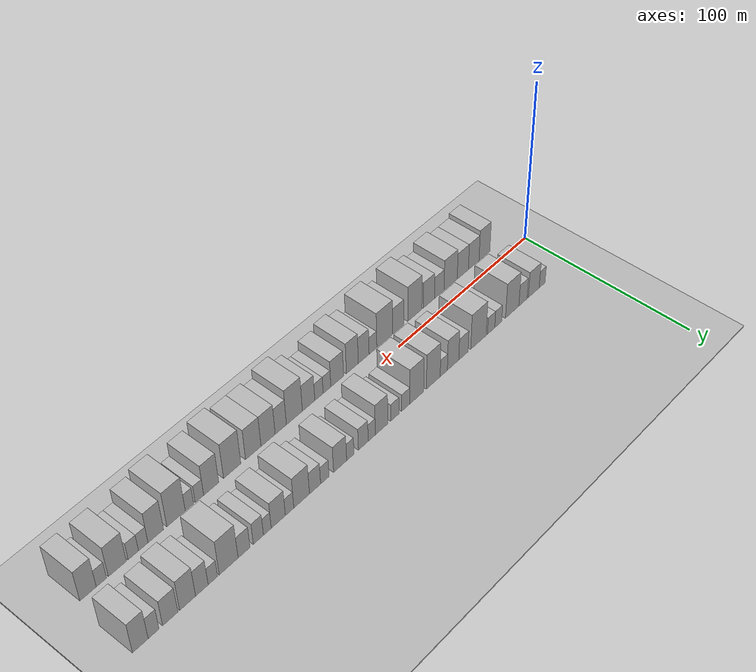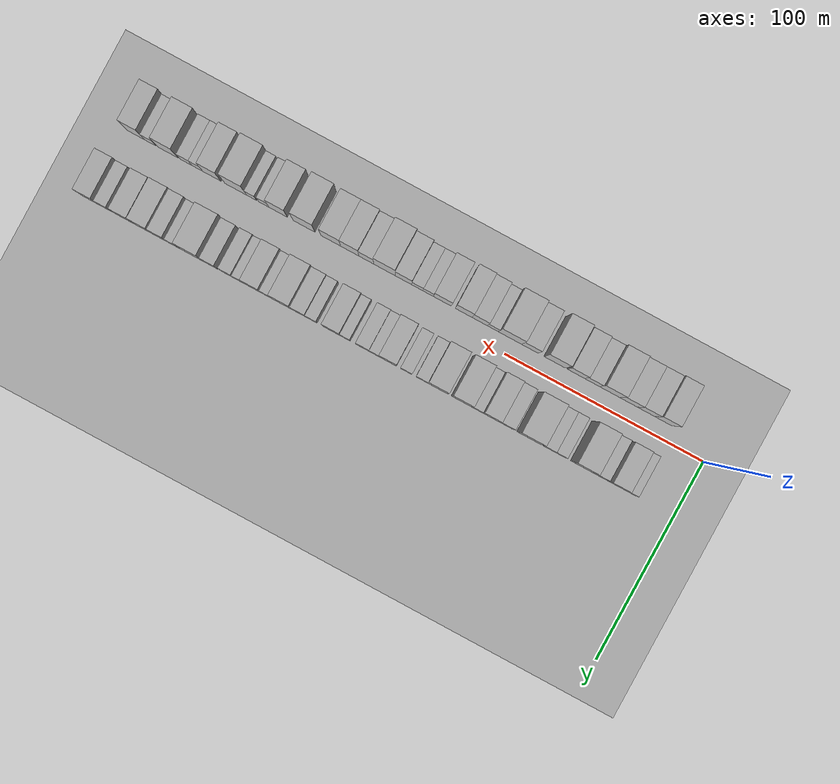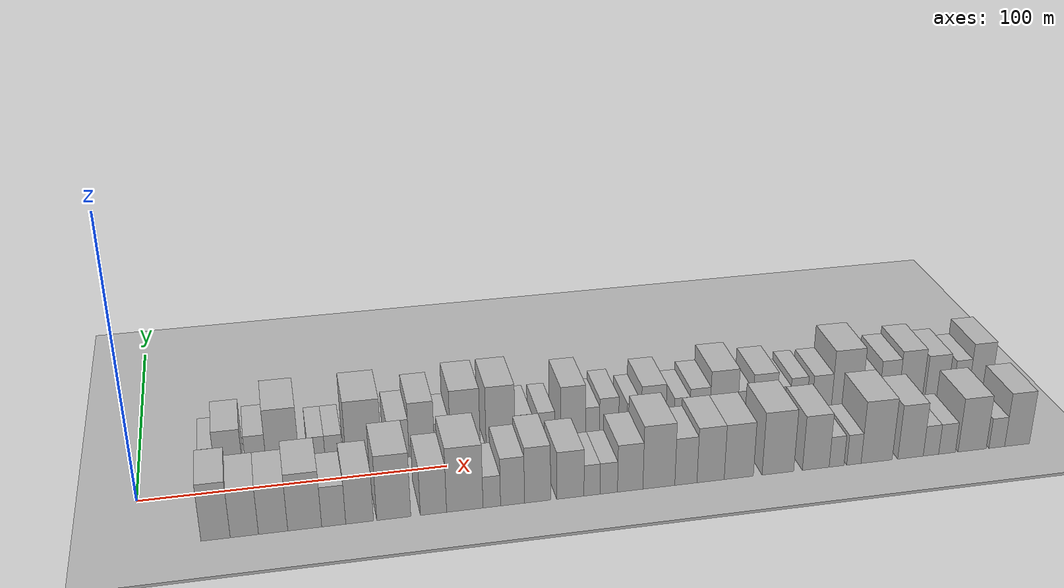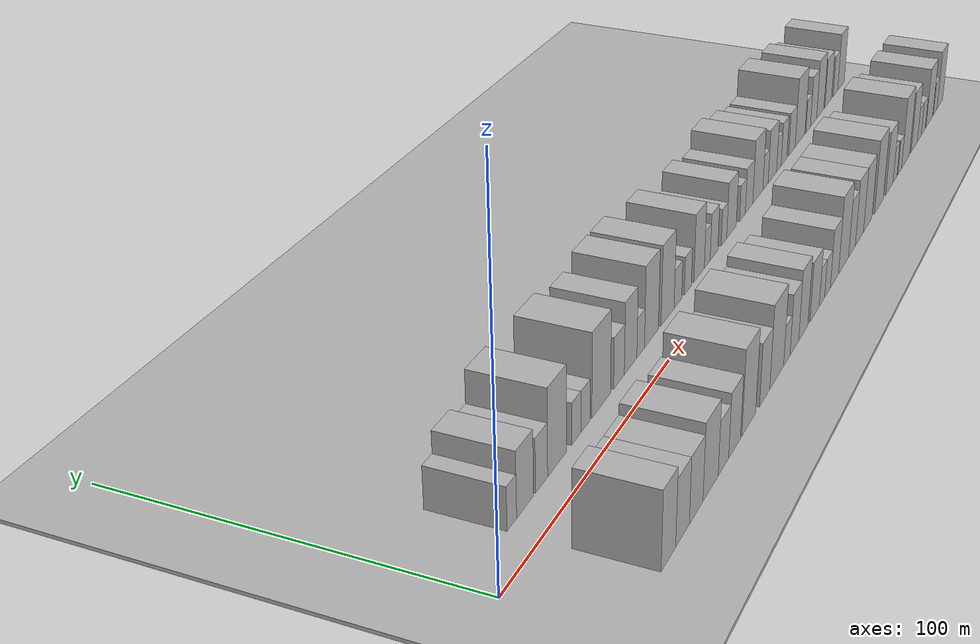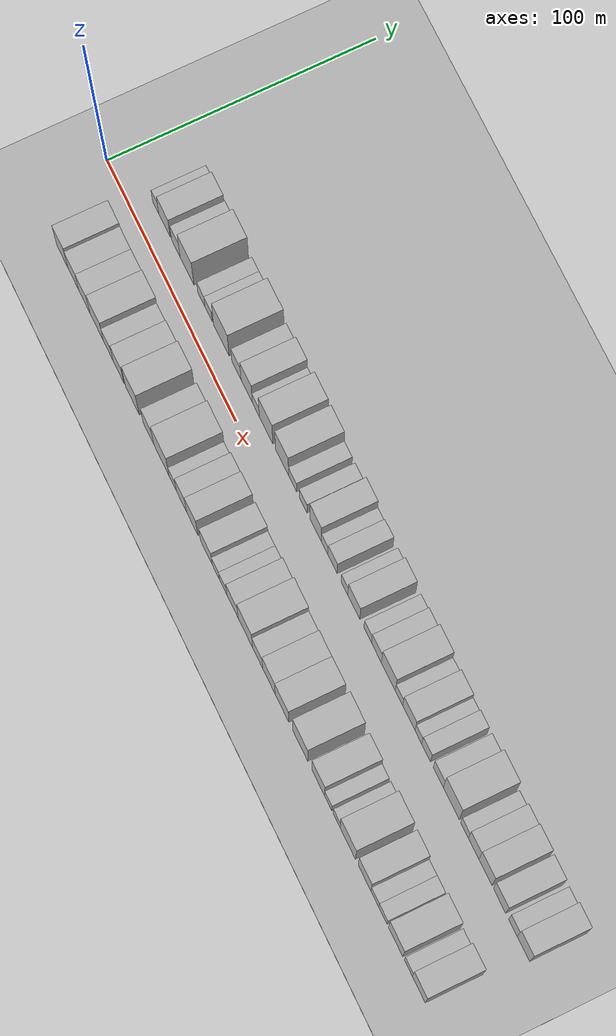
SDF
<?xml version="1.0" encoding="utf-8"?>

<sdf version="1.6">

   <world name="default">

      <gui fullscreen="0">

         <camera name="user_camera">

            <pose>-15 0 4.57585 0 0 0</pose>

            <view_controller>orbit</view_controller>

         </camera>

      </gui>

      <scene>

         <sky>

           <clouds>

             <speed>12</speed>

           </clouds>

         </sky>

         <ambient>0.4 0.4 0.4 1</ambient>

         <background>0.7 0.7 0.7 1</background>

         <shadows>1</shadows>

      </scene>

      <gravity>0 0 -9.8066</gravity>

      <magnetic_field>6e-06 2.3e-05 -4.2e-05</magnetic_field>

      <physics default="0" name="default_physics" type="ode">

         <ode>

            <solver>

               <type>quick</type>

               <iters>10</iters>

               <sor>1.0</sor>

               <use_dynamic_moi_rescaling>0</use_dynamic_moi_rescaling>

            </solver>

            <constraints>

               <cfm>0</cfm>

               <erp>0.2</erp>

               <contact_max_correcting_vel>100</contact_max_correcting_vel>

               <contact_surface_layer>0.001</contact_surface_layer>

            </constraints>

         </ode>

         <max_step_size>0.004</max_step_size>

         <real_time_factor>1</real_time_factor>

         <real_time_update_rate>250</real_time_update_rate>

      </physics>

      <light name="sun" type="directional">

         <cast_shadows>1</cast_shadows>

         <pose>0 0 10 0 0 0</pose>

         <diffuse>0.8 0.8 0.8 1</diffuse>

         <specular>0.2 0.2 0.2 1</specular>

         <attenuation>

            <range>1000</range>

            <constant>0.9</constant>

            <linear>0.01</linear>

            <quadratic>0.001</quadratic>

         </attenuation>

         <direction>-0.5 0.1 -0.9</direction>

      </light>

      <include>

         <name>ground_plane_1</name>

         <uri>model://HANNAS_ground_plane</uri>

         <pose>0 0 0  0 0 0</pose>

      </include>

      <include>

         <name>ground_plane_2</name>

         <uri>model://HANNAS_ground_plane</uri>

         <pose>100 0 0  0 0 0</pose>

      </include>

      <model name="building_1">

         <static>1</static>

         <pose frame="">22.4371 17.5000 0 0.000000 0.000000 1.570796</pose>

         <link name="link">

            <pose frame="">0 0 6.00 0 0 0</pose>

            <collision name="collision">

               <geometry>

                  <box>

                     <size>20.0000 4.8741 12.0000</size>

                  </box>

               </geometry>

               <max_contacts>10</max_contacts>

               <surface>

                  <contact>

                     <ode/>

                  </contact>

                  <bounce/>

                  <friction>

                     <torsional>

                        <ode/>

                     </torsional>

                     <ode/>

                  </friction>

               </surface>

            </collision>

            <visual name="visual">

               <cast_shadows>0</cast_shadows>

               <geometry>

                  <box>

                     <size>20.0000 4.8741 12.0000</size>

                  </box>

               </geometry>

               <material>

                  <script>

                     <uri>model://HANNAS_wall/materials/scripts</uri>

                     <uri>model://HANNAS_wall/materials/textures</uri>

                     <name>vrc/HANNAS_wall</name>

                  </script>

               </material>

            </visual>

            <self_collide>0</self_collide>

            <enable_wind>0</enable_wind>

            <kinematic>0</kinematic>

         </link>

      </model>

      <model name="building_2">

         <static>1</static>

         <pose frame="">29.3461 17.5000 0 0.000000 0.000000 1.570796</pose>

         <link name="link">

            <pose frame="">0 0 9.00 0 0 0</pose>

            <collision name="collision">

               <geometry>

                  <box>

                     <size>20.0000 8.9441 18.0000</size>

                  </box>

               </geometry>

               <max_contacts>10</max_contacts>

               <surface>

                  <contact>

                     <ode/>

                  </contact>

                  <bounce/>

                  <friction>

                     <torsional>

                        <ode/>

                     </torsional>

                     <ode/>

                  </friction>

               </surface>

            </collision>

            <visual name="visual">

               <cast_shadows>0</cast_shadows>

               <geometry>

                  <box>

                     <size>20.0000 8.9441 18.0000</size>

                  </box>

               </geometry>

               <material>

                  <script>

                     <uri>model://HANNAS_wall/materials/scripts</uri>

                     <uri>model://HANNAS_wall/materials/textures</uri>

                     <name>vrc/HANNAS_wall</name>

                  </script>

               </material>

            </visual>

            <self_collide>0</self_collide>

            <enable_wind>0</enable_wind>

            <kinematic>0</kinematic>

         </link>

      </model>

      <model name="building_3">

         <static>1</static>

         <pose frame="">38.1417 17.5000 0 0.000000 0.000000 1.570796</pose>

         <link name="link">

            <pose frame="">0 0 7.50 0 0 0</pose>

            <collision name="collision">

               <geometry>

                  <box>

                     <size>20.0000 6.6471 15.0000</size>

                  </box>

               </geometry>

               <max_contacts>10</max_contacts>

               <surface>

                  <contact>

                     <ode/>

                  </contact>

                  <bounce/>

                  <friction>

                     <torsional>

                        <ode/>

                     </torsional>

                     <ode/>

                  </friction>

               </surface>

            </collision>

            <visual name="visual">

               <cast_shadows>0</cast_shadows>

               <geometry>

                  <box>

                     <size>20.0000 6.6471 15.0000</size>

                  </box>

               </geometry>

               <material>

                  <script>

                     <uri>model://HANNAS_wall/materials/scripts</uri>

                     <uri>model://HANNAS_wall/materials/textures</uri>

                     <name>vrc/HANNAS_wall</name>

                  </script>

               </material>

            </visual>

            <self_collide>0</self_collide>

            <enable_wind>0</enable_wind>

            <kinematic>0</kinematic>

         </link>

      </model>

      <model name="building_4">

         <static>1</static>

         <pose frame="">46.8133 17.5000 0 0.000000 0.000000 1.570796</pose>

         <link name="link">

            <pose frame="">0 0 12.00 0 0 0</pose>

            <collision name="collision">

               <geometry>

                  <box>

                     <size>20.0000 10.6961 24.0000</size>

                  </box>

               </geometry>

               <max_contacts>10</max_contacts>

               <surface>

                  <contact>

                     <ode/>

                  </contact>

                  <bounce/>

                  <friction>

                     <torsional>

                        <ode/>

                     </torsional>

                     <ode/>

                  </friction>

               </surface>

            </collision>

            <visual name="visual">

               <cast_shadows>0</cast_shadows>

               <geometry>

                  <box>

                     <size>20.0000 10.6961 24.0000</size>

                  </box>

               </geometry>

               <material>

                  <script>

                     <uri>model://HANNAS_wall/materials/scripts</uri>

                     <uri>model://HANNAS_wall/materials/textures</uri>

                     <name>vrc/HANNAS_wall</name>

                  </script>

               </material>

            </visual>

            <self_collide>0</self_collide>

            <enable_wind>0</enable_wind>

            <kinematic>0</kinematic>

         </link>

      </model>

      <model name="building_5">

         <static>1</static>

         <pose frame="">57.8785 17.5000 0 0.000000 0.000000 1.570796</pose>

         <link name="link">

            <pose frame="">0 0 6.00 0 0 0</pose>

            <collision name="collision">

               <geometry>

                  <box>

                     <size>20.0000 5.4343 12.0000</size>

                  </box>

               </geometry>

               <max_contacts>10</max_contacts>

               <surface>

                  <contact>

                     <ode/>

                  </contact>

                  <bounce/>

                  <friction>

                     <torsional>

                        <ode/>

                     </torsional>

                     <ode/>

                  </friction>

               </surface>

            </collision>

            <visual name="visual">

               <cast_shadows>0</cast_shadows>

               <geometry>

                  <box>

                     <size>20.0000 5.4343 12.0000</size>

                  </box>

               </geometry>

               <material>

                  <script>

                     <uri>model://HANNAS_wall/materials/scripts</uri>

                     <uri>model://HANNAS_wall/materials/textures</uri>

                     <name>vrc/HANNAS_wall</name>

                  </script>

               </material>

            </visual>

            <self_collide>0</self_collide>

            <enable_wind>0</enable_wind>

            <kinematic>0</kinematic>

         </link>

      </model>

      <model name="building_6">

         <static>1</static>

         <pose frame="">63.4660 17.5000 0 0.000000 0.000000 1.570796</pose>

         <link name="link">

            <pose frame="">0 0 6.00 0 0 0</pose>

            <collision name="collision">

               <geometry>

                  <box>

                     <size>20.0000 5.7407 12.0000</size>

                  </box>

               </geometry>

               <max_contacts>10</max_contacts>

               <surface>

                  <contact>

                     <ode/>

                  </contact>

                  <bounce/>

                  <friction>

                     <torsional>

                        <ode/>

                     </torsional>

                     <ode/>

                  </friction>

               </surface>

            </collision>

            <visual name="visual">

               <cast_shadows>0</cast_shadows>

               <geometry>

                  <box>

                     <size>20.0000 5.7407 12.0000</size>

                  </box>

               </geometry>

               <material>

                  <script>

                     <uri>model://HANNAS_wall/materials/scripts</uri>

                     <uri>model://HANNAS_wall/materials/textures</uri>

                     <name>vrc/HANNAS_wall</name>

                  </script>

               </material>

            </visual>

            <self_collide>0</self_collide>

            <enable_wind>0</enable_wind>

            <kinematic>0</kinematic>

         </link>

      </model>

      <model name="building_7">

         <static>1</static>

         <pose frame="">73.2834 17.5000 0 0.000000 0.000000 1.570796</pose>

         <link name="link">

            <pose frame="">0 0 12.00 0 0 0</pose>

            <collision name="collision">

               <geometry>

                  <box>

                     <size>20.0000 11.8941 24.0000</size>

                  </box>

               </geometry>

               <max_contacts>10</max_contacts>

               <surface>

                  <contact>

                     <ode/>

                  </contact>

                  <bounce/>

                  <friction>

                     <torsional>

                        <ode/>

                     </torsional>

                     <ode/>

                  </friction>

               </surface>

            </collision>

            <visual name="visual">

               <cast_shadows>0</cast_shadows>

               <geometry>

                  <box>

                     <size>20.0000 11.8941 24.0000</size>

                  </box>

               </geometry>

               <material>

                  <script>

                     <uri>model://HANNAS_wall/materials/scripts</uri>

                     <uri>model://HANNAS_wall/materials/textures</uri>

                     <name>vrc/HANNAS_wall</name>

                  </script>

               </material>

            </visual>

            <self_collide>0</self_collide>

            <enable_wind>0</enable_wind>

            <kinematic>0</kinematic>

         </link>

      </model>

      <model name="building_8">

         <static>1</static>

         <pose frame="">84.7820 17.5000 0 0.000000 0.000000 1.570796</pose>

         <link name="link">

            <pose frame="">0 0 7.50 0 0 0</pose>

            <collision name="collision">

               <geometry>

                  <box>

                     <size>20.0000 7.1030 15.0000</size>

                  </box>

               </geometry>

               <max_contacts>10</max_contacts>

               <surface>

                  <contact>

                     <ode/>

                  </contact>

                  <bounce/>

                  <friction>

                     <torsional>

                        <ode/>

                     </torsional>

                     <ode/>

                  </friction>

               </surface>

            </collision>

            <visual name="visual">

               <cast_shadows>0</cast_shadows>

               <geometry>

                  <box>

                     <size>20.0000 7.1030 15.0000</size>

                  </box>

               </geometry>

               <material>

                  <script>

                     <uri>model://HANNAS_wall/materials/scripts</uri>

                     <uri>model://HANNAS_wall/materials/textures</uri>

                     <name>vrc/HANNAS_wall</name>

                  </script>

               </material>

            </visual>

            <self_collide>0</self_collide>

            <enable_wind>0</enable_wind>

            <kinematic>0</kinematic>

         </link>

      </model>

      <model name="building_9">

         <static>1</static>

         <pose frame="">92.6144 17.5000 0 0.000000 0.000000 1.570796</pose>

         <link name="link">

            <pose frame="">0 0 10.50 0 0 0</pose>

            <collision name="collision">

               <geometry>

                  <box>

                     <size>20.0000 8.5619 21.0000</size>

                  </box>

               </geometry>

               <max_contacts>10</max_contacts>

               <surface>

                  <contact>

                     <ode/>

                  </contact>

                  <bounce/>

                  <friction>

                     <torsional>

                        <ode/>

                     </torsional>

                     <ode/>

                  </friction>

               </surface>

            </collision>

            <visual name="visual">

               <cast_shadows>0</cast_shadows>

               <geometry>

                  <box>

                     <size>20.0000 8.5619 21.0000</size>

                  </box>

               </geometry>

               <material>

                  <script>

                     <uri>model://HANNAS_wall/materials/scripts</uri>

                     <uri>model://HANNAS_wall/materials/textures</uri>

                     <name>vrc/HANNAS_wall</name>

                  </script>

               </material>

            </visual>

            <self_collide>0</self_collide>

            <enable_wind>0</enable_wind>

            <kinematic>0</kinematic>

         </link>

      </model>

      <model name="building_10">

         <static>1</static>

         <pose frame="">99.5759 17.5000 0 0.000000 0.000000 1.570796</pose>

         <link name="link">

            <pose frame="">0 0 6.00 0 0 0</pose>

            <collision name="collision">

               <geometry>

                  <box>

                     <size>20.0000 5.3610 12.0000</size>

                  </box>

               </geometry>

               <max_contacts>10</max_contacts>

               <surface>

                  <contact>

                     <ode/>

                  </contact>

                  <bounce/>

                  <friction>

                     <torsional>

                        <ode/>

                     </torsional>

                     <ode/>

                  </friction>

               </surface>

            </collision>

            <visual name="visual">

               <cast_shadows>0</cast_shadows>

               <geometry>

                  <box>

                     <size>20.0000 5.3610 12.0000</size>

                  </box>

               </geometry>

               <material>

                  <script>

                     <uri>model://HANNAS_wall/materials/scripts</uri>

                     <uri>model://HANNAS_wall/materials/textures</uri>

                     <name>vrc/HANNAS_wall</name>

                  </script>

               </material>

            </visual>

            <self_collide>0</self_collide>

            <enable_wind>0</enable_wind>

            <kinematic>0</kinematic>

         </link>

      </model>

      <model name="building_11">

         <static>1</static>

         <pose frame="">107.3028 17.5000 0 0.000000 0.000000 1.570796</pose>

         <link name="link">

            <pose frame="">0 0 12.00 0 0 0</pose>

            <collision name="collision">

               <geometry>

                  <box>

                     <size>20.0000 10.0929 24.0000</size>

                  </box>

               </geometry>

               <max_contacts>10</max_contacts>

               <surface>

                  <contact>

                     <ode/>

                  </contact>

                  <bounce/>

                  <friction>

                     <torsional>

                        <ode/>

                     </torsional>

                     <ode/>

                  </friction>

               </surface>

            </collision>

            <visual name="visual">

               <cast_shadows>0</cast_shadows>

               <geometry>

                  <box>

                     <size>20.0000 10.0929 24.0000</size>

                  </box>

               </geometry>

               <material>

                  <script>

                     <uri>model://HANNAS_wall/materials/scripts</uri>

                     <uri>model://HANNAS_wall/materials/textures</uri>

                     <name>vrc/HANNAS_wall</name>

                  </script>

               </material>

            </visual>

            <self_collide>0</self_collide>

            <enable_wind>0</enable_wind>

            <kinematic>0</kinematic>

         </link>

      </model>

      <model name="building_12">

         <static>1</static>

         <pose frame="">119.2989 17.5000 0 0.000000 0.000000 1.570796</pose>

         <link name="link">

            <pose frame="">0 0 12.00 0 0 0</pose>

            <collision name="collision">

               <geometry>

                  <box>

                     <size>20.0000 9.8993 24.0000</size>

                  </box>

               </geometry>

               <max_contacts>10</max_contacts>

               <surface>

                  <contact>

                     <ode/>

                  </contact>

                  <bounce/>

                  <friction>

                     <torsional>

                        <ode/>

                     </torsional>

                     <ode/>

                  </friction>

               </surface>

            </collision>

            <visual name="visual">

               <cast_shadows>0</cast_shadows>

               <geometry>

                  <box>

                     <size>20.0000 9.8993 24.0000</size>

                  </box>

               </geometry>

               <material>

                  <script>

                     <uri>model://HANNAS_wall/materials/scripts</uri>

                     <uri>model://HANNAS_wall/materials/textures</uri>

                     <name>vrc/HANNAS_wall</name>

                  </script>

               </material>

            </visual>

            <self_collide>0</self_collide>

            <enable_wind>0</enable_wind>

            <kinematic>0</kinematic>

         </link>

      </model>

      <model name="building_13">

         <static>1</static>

         <pose frame="">127.2059 17.5000 0 0.000000 0.000000 1.570796</pose>

         <link name="link">

            <pose frame="">0 0 6.00 0 0 0</pose>

            <collision name="collision">

               <geometry>

                  <box>

                     <size>20.0000 5.9146 12.0000</size>

                  </box>

               </geometry>

               <max_contacts>10</max_contacts>

               <surface>

                  <contact>

                     <ode/>

                  </contact>

                  <bounce/>

                  <friction>

                     <torsional>

                        <ode/>

                     </torsional>

                     <ode/>

                  </friction>

               </surface>

            </collision>

            <visual name="visual">

               <cast_shadows>0</cast_shadows>

               <geometry>

                  <box>

                     <size>20.0000 5.9146 12.0000</size>

                  </box>

               </geometry>

               <material>

                  <script>

                     <uri>model://HANNAS_wall/materials/scripts</uri>

                     <uri>model://HANNAS_wall/materials/textures</uri>

                     <name>vrc/HANNAS_wall</name>

                  </script>

               </material>

            </visual>

            <self_collide>0</self_collide>

            <enable_wind>0</enable_wind>

            <kinematic>0</kinematic>

         </link>

      </model>

      <model name="building_14">

         <static>1</static>

         <pose frame="">135.0609 17.5000 0 0.000000 0.000000 1.570796</pose>

         <link name="link">

            <pose frame="">0 0 6.00 0 0 0</pose>

            <collision name="collision">

               <geometry>

                  <box>

                     <size>20.0000 5.7954 12.0000</size>

                  </box>

               </geometry>

               <max_contacts>10</max_contacts>

               <surface>

                  <contact>

                     <ode/>

                  </contact>

                  <bounce/>

                  <friction>

                     <torsional>

                        <ode/>

                     </torsional>

                     <ode/>

                  </friction>

               </surface>

            </collision>

            <visual name="visual">

               <cast_shadows>0</cast_shadows>

               <geometry>

                  <box>

                     <size>20.0000 5.7954 12.0000</size>

                  </box>

               </geometry>

               <material>

                  <script>

                     <uri>model://HANNAS_wall/materials/scripts</uri>

                     <uri>model://HANNAS_wall/materials/textures</uri>

                     <name>vrc/HANNAS_wall</name>

                  </script>

               </material>

            </visual>

            <self_collide>0</self_collide>

            <enable_wind>0</enable_wind>

            <kinematic>0</kinematic>

         </link>

      </model>

      <model name="building_15">

         <static>1</static>

         <pose frame="">144.3010 17.5000 0 0.000000 0.000000 1.570796</pose>

         <link name="link">

            <pose frame="">0 0 10.50 0 0 0</pose>

            <collision name="collision">

               <geometry>

                  <box>

                     <size>20.0000 8.6849 21.0000</size>

                  </box>

               </geometry>

               <max_contacts>10</max_contacts>

               <surface>

                  <contact>

                     <ode/>

                  </contact>

                  <bounce/>

                  <friction>

                     <torsional>

                        <ode/>

                     </torsional>

                     <ode/>

                  </friction>

               </surface>

            </collision>

            <visual name="visual">

               <cast_shadows>0</cast_shadows>

               <geometry>

                  <box>

                     <size>20.0000 8.6849 21.0000</size>

                  </box>

               </geometry>

               <material>

                  <script>

                     <uri>model://HANNAS_wall/materials/scripts</uri>

                     <uri>model://HANNAS_wall/materials/textures</uri>

                     <name>vrc/HANNAS_wall</name>

                  </script>

               </material>

            </visual>

            <self_collide>0</self_collide>

            <enable_wind>0</enable_wind>

            <kinematic>0</kinematic>

         </link>

      </model>

      <model name="building_16">

         <static>1</static>

         <pose frame="">151.1096 17.5000 0 0.000000 0.000000 1.570796</pose>

         <link name="link">

            <pose frame="">0 0 6.00 0 0 0</pose>

            <collision name="collision">

               <geometry>

                  <box>

                     <size>20.0000 4.9323 12.0000</size>

                  </box>

               </geometry>

               <max_contacts>10</max_contacts>

               <surface>

                  <contact>

                     <ode/>

                  </contact>

                  <bounce/>

                  <friction>

                     <torsional>

                        <ode/>

                     </torsional>

                     <ode/>

                  </friction>

               </surface>

            </collision>

            <visual name="visual">

               <cast_shadows>0</cast_shadows>

               <geometry>

                  <box>

                     <size>20.0000 4.9323 12.0000</size>

                  </box>

               </geometry>

               <material>

                  <script>

                     <uri>model://HANNAS_wall/materials/scripts</uri>

                     <uri>model://HANNAS_wall/materials/textures</uri>

                     <name>vrc/HANNAS_wall</name>

                  </script>

               </material>

            </visual>

            <self_collide>0</self_collide>

            <enable_wind>0</enable_wind>

            <kinematic>0</kinematic>

         </link>

      </model>

      <model name="building_17">

         <static>1</static>

         <pose frame="">156.9179 17.5000 0 0.000000 0.000000 1.570796</pose>

         <link name="link">

            <pose frame="">0 0 7.50 0 0 0</pose>

            <collision name="collision">

               <geometry>

                  <box>

                     <size>20.0000 6.6842 15.0000</size>

                  </box>

               </geometry>

               <max_contacts>10</max_contacts>

               <surface>

                  <contact>

                     <ode/>

                  </contact>

                  <bounce/>

                  <friction>

                     <torsional>

                        <ode/>

                     </torsional>

                     <ode/>

                  </friction>

               </surface>

            </collision>

            <visual name="visual">

               <cast_shadows>0</cast_shadows>

               <geometry>

                  <box>

                     <size>20.0000 6.6842 15.0000</size>

                  </box>

               </geometry>

               <material>

                  <script>

                     <uri>model://HANNAS_wall/materials/scripts</uri>

                     <uri>model://HANNAS_wall/materials/textures</uri>

                     <name>vrc/HANNAS_wall</name>

                  </script>

               </material>

            </visual>

            <self_collide>0</self_collide>

            <enable_wind>0</enable_wind>

            <kinematic>0</kinematic>

         </link>

      </model>

      <model name="building_18">

         <static>1</static>

         <pose frame="">165.7371 17.5000 0 0.000000 0.000000 1.570796</pose>

         <link name="link">

            <pose frame="">0 0 6.00 0 0 0</pose>

            <collision name="collision">

               <geometry>

                  <box>

                     <size>20.0000 4.9541 12.0000</size>

                  </box>

               </geometry>

               <max_contacts>10</max_contacts>

               <surface>

                  <contact>

                     <ode/>

                  </contact>

                  <bounce/>

                  <friction>

                     <torsional>

                        <ode/>

                     </torsional>

                     <ode/>

                  </friction>

               </surface>

            </collision>

            <visual name="visual">

               <cast_shadows>0</cast_shadows>

               <geometry>

                  <box>

                     <size>20.0000 4.9541 12.0000</size>

                  </box>

               </geometry>

               <material>

                  <script>

                     <uri>model://HANNAS_wall/materials/scripts</uri>

                     <uri>model://HANNAS_wall/materials/textures</uri>

                     <name>vrc/HANNAS_wall</name>

                  </script>

               </material>

            </visual>

            <self_collide>0</self_collide>

            <enable_wind>0</enable_wind>

            <kinematic>0</kinematic>

         </link>

      </model>

      <model name="building_19">

         <static>1</static>

         <pose frame="">172.5716 17.5000 0 0.000000 0.000000 1.570796</pose>

         <link name="link">

            <pose frame="">0 0 9.00 0 0 0</pose>

            <collision name="collision">

               <geometry>

                  <box>

                     <size>20.0000 8.7150 18.0000</size>

                  </box>

               </geometry>

               <max_contacts>10</max_contacts>

               <surface>

                  <contact>

                     <ode/>

                  </contact>

                  <bounce/>

                  <friction>

                     <torsional>

                        <ode/>

                     </torsional>

                     <ode/>

                  </friction>

               </surface>

            </collision>

            <visual name="visual">

               <cast_shadows>0</cast_shadows>

               <geometry>

                  <box>

                     <size>20.0000 8.7150 18.0000</size>

                  </box>

               </geometry>

               <material>

                  <script>

                     <uri>model://HANNAS_wall/materials/scripts</uri>

                     <uri>model://HANNAS_wall/materials/textures</uri>

                     <name>vrc/HANNAS_wall</name>

                  </script>

               </material>

            </visual>

            <self_collide>0</self_collide>

            <enable_wind>0</enable_wind>

            <kinematic>0</kinematic>

         </link>

      </model>

      <model name="building_20">

         <static>1</static>

         <pose frame="">182.6954 17.5000 0 0.000000 0.000000 1.570796</pose>

         <link name="link">

            <pose frame="">0 0 6.00 0 0 0</pose>

            <collision name="collision">

               <geometry>

                  <box>

                     <size>20.0000 5.5326 12.0000</size>

                  </box>

               </geometry>

               <max_contacts>10</max_contacts>

               <surface>

                  <contact>

                     <ode/>

                  </contact>

                  <bounce/>

                  <friction>

                     <torsional>

                        <ode/>

                     </torsional>

                     <ode/>

                  </friction>

               </surface>

            </collision>

            <visual name="visual">

               <cast_shadows>0</cast_shadows>

               <geometry>

                  <box>

                     <size>20.0000 5.5326 12.0000</size>

                  </box>

               </geometry>

               <material>

                  <script>

                     <uri>model://HANNAS_wall/materials/scripts</uri>

                     <uri>model://HANNAS_wall/materials/textures</uri>

                     <name>vrc/HANNAS_wall</name>

                  </script>

               </material>

            </visual>

            <self_collide>0</self_collide>

            <enable_wind>0</enable_wind>

            <kinematic>0</kinematic>

         </link>

      </model>

      <model name="building_21">

         <static>1</static>

         <pose frame="">189.0813 17.5000 0 0.000000 0.000000 1.570796</pose>

         <link name="link">

            <pose frame="">0 0 7.50 0 0 0</pose>

            <collision name="collision">

               <geometry>

                  <box>

                     <size>20.0000 7.2392 15.0000</size>

                  </box>

               </geometry>

               <max_contacts>10</max_contacts>

               <surface>

                  <contact>

                     <ode/>

                  </contact>

                  <bounce/>

                  <friction>

                     <torsional>

                        <ode/>

                     </torsional>

                     <ode/>

                  </friction>

               </surface>

            </collision>

            <visual name="visual">

               <cast_shadows>0</cast_shadows>

               <geometry>

                  <box>

                     <size>20.0000 7.2392 15.0000</size>

                  </box>

               </geometry>

               <material>

                  <script>

                     <uri>model://HANNAS_wall/materials/scripts</uri>

                     <uri>model://HANNAS_wall/materials/textures</uri>

                     <name>vrc/HANNAS_wall</name>

                  </script>

               </material>

            </visual>

            <self_collide>0</self_collide>

            <enable_wind>0</enable_wind>

            <kinematic>0</kinematic>

         </link>

      </model>

      <model name="building_22">

         <static>1</static>

         <pose frame="">197.7190 17.5000 0 0.000000 0.000000 1.570796</pose>

         <link name="link">

            <pose frame="">0 0 10.50 0 0 0</pose>

            <collision name="collision">

               <geometry>

                  <box>

                     <size>20.0000 10.0362 21.0000</size>

                  </box>

               </geometry>

               <max_contacts>10</max_contacts>

               <surface>

                  <contact>

                     <ode/>

                  </contact>

                  <bounce/>

                  <friction>

                     <torsional>

                        <ode/>

                     </torsional>

                     <ode/>

                  </friction>

               </surface>

            </collision>

            <visual name="visual">

               <cast_shadows>0</cast_shadows>

               <geometry>

                  <box>

                     <size>20.0000 10.0362 21.0000</size>

                  </box>

               </geometry>

               <material>

                  <script>

                     <uri>model://HANNAS_wall/materials/scripts</uri>

                     <uri>model://HANNAS_wall/materials/textures</uri>

                     <name>vrc/HANNAS_wall</name>

                  </script>

               </material>

            </visual>

            <self_collide>0</self_collide>

            <enable_wind>0</enable_wind>

            <kinematic>0</kinematic>

         </link>

      </model>

      <model name="building_23">

         <static>1</static>

         <pose frame="">205.4231 17.5000 0 0.000000 0.000000 1.570796</pose>

         <link name="link">

            <pose frame="">0 0 6.00 0 0 0</pose>

            <collision name="collision">

               <geometry>

                  <box>

                     <size>20.0000 5.3720 12.0000</size>

                  </box>

               </geometry>

               <max_contacts>10</max_contacts>

               <surface>

                  <contact>

                     <ode/>

                  </contact>

                  <bounce/>

                  <friction>

                     <torsional>

                        <ode/>

                     </torsional>

                     <ode/>

                  </friction>

               </surface>

            </collision>

            <visual name="visual">

               <cast_shadows>0</cast_shadows>

               <geometry>

                  <box>

                     <size>20.0000 5.3720 12.0000</size>

                  </box>

               </geometry>

               <material>

                  <script>

                     <uri>model://HANNAS_wall/materials/scripts</uri>

                     <uri>model://HANNAS_wall/materials/textures</uri>

                     <name>vrc/HANNAS_wall</name>

                  </script>

               </material>

            </visual>

            <self_collide>0</self_collide>

            <enable_wind>0</enable_wind>

            <kinematic>0</kinematic>

         </link>

      </model>

      <model name="building_24">

         <static>1</static>

         <pose frame="">212.5330 17.5000 0 0.000000 0.000000 1.570796</pose>

         <link name="link">

            <pose frame="">0 0 9.00 0 0 0</pose>

            <collision name="collision">

               <geometry>

                  <box>

                     <size>20.0000 8.8478 18.0000</size>

                  </box>

               </geometry>

               <max_contacts>10</max_contacts>

               <surface>

                  <contact>

                     <ode/>

                  </contact>

                  <bounce/>

                  <friction>

                     <torsional>

                        <ode/>

                     </torsional>

                     <ode/>

                  </friction>

               </surface>

            </collision>

            <visual name="visual">

               <cast_shadows>0</cast_shadows>

               <geometry>

                  <box>

                     <size>20.0000 8.8478 18.0000</size>

                  </box>

               </geometry>

               <material>

                  <script>

                     <uri>model://HANNAS_wall/materials/scripts</uri>

                     <uri>model://HANNAS_wall/materials/textures</uri>

                     <name>vrc/HANNAS_wall</name>

                  </script>

               </material>

            </visual>

            <self_collide>0</self_collide>

            <enable_wind>0</enable_wind>

            <kinematic>0</kinematic>

         </link>

      </model>

      <model name="building_25">

         <static>1</static>

         <pose frame="">219.3703 17.5000 0 0.000000 0.000000 1.570796</pose>

         <link name="link">

            <pose frame="">0 0 6.00 0 0 0</pose>

            <collision name="collision">

               <geometry>

                  <box>

                     <size>20.0000 4.8268 12.0000</size>

                  </box>

               </geometry>

               <max_contacts>10</max_contacts>

               <surface>

                  <contact>

                     <ode/>

                  </contact>

                  <bounce/>

                  <friction>

                     <torsional>

                        <ode/>

                     </torsional>

                     <ode/>

                  </friction>

               </surface>

            </collision>

            <visual name="visual">

               <cast_shadows>0</cast_shadows>

               <geometry>

                  <box>

                     <size>20.0000 4.8268 12.0000</size>

                  </box>

               </geometry>

               <material>

                  <script>

                     <uri>model://HANNAS_wall/materials/scripts</uri>

                     <uri>model://HANNAS_wall/materials/textures</uri>

                     <name>vrc/HANNAS_wall</name>

                  </script>

               </material>

            </visual>

            <self_collide>0</self_collide>

            <enable_wind>0</enable_wind>

            <kinematic>0</kinematic>

         </link>

      </model>

      <model name="building_26">

         <static>1</static>

         <pose frame="">224.9114 17.5000 0 0.000000 0.000000 1.570796</pose>

         <link name="link">

            <pose frame="">0 0 7.50 0 0 0</pose>

            <collision name="collision">

               <geometry>

                  <box>

                     <size>20.0000 6.2554 15.0000</size>

                  </box>

               </geometry>

               <max_contacts>10</max_contacts>

               <surface>

                  <contact>

                     <ode/>

                  </contact>

                  <bounce/>

                  <friction>

                     <torsional>

                        <ode/>

                     </torsional>

                     <ode/>

                  </friction>

               </surface>

            </collision>

            <visual name="visual">

               <cast_shadows>0</cast_shadows>

               <geometry>

                  <box>

                     <size>20.0000 6.2554 15.0000</size>

                  </box>

               </geometry>

               <material>

                  <script>

                     <uri>model://HANNAS_wall/materials/scripts</uri>

                     <uri>model://HANNAS_wall/materials/textures</uri>

                     <name>vrc/HANNAS_wall</name>

                  </script>

               </material>

            </visual>

            <self_collide>0</self_collide>

            <enable_wind>0</enable_wind>

            <kinematic>0</kinematic>

         </link>

      </model>

      <model name="building_27">

         <static>1</static>

         <pose frame="">233.6453 17.5000 0 0.000000 0.000000 1.570796</pose>

         <link name="link">

            <pose frame="">0 0 7.50 0 0 0</pose>

            <collision name="collision">

               <geometry>

                  <box>

                     <size>20.0000 7.2123 15.0000</size>

                  </box>

               </geometry>

               <max_contacts>10</max_contacts>

               <surface>

                  <contact>

                     <ode/>

                  </contact>

                  <bounce/>

                  <friction>

                     <torsional>

                        <ode/>

                     </torsional>

                     <ode/>

                  </friction>

               </surface>

            </collision>

            <visual name="visual">

               <cast_shadows>0</cast_shadows>

               <geometry>

                  <box>

                     <size>20.0000 7.2123 15.0000</size>

                  </box>

               </geometry>

               <material>

                  <script>

                     <uri>model://HANNAS_wall/materials/scripts</uri>

                     <uri>model://HANNAS_wall/materials/textures</uri>

                     <name>vrc/HANNAS_wall</name>

                  </script>

               </material>

            </visual>

            <self_collide>0</self_collide>

            <enable_wind>0</enable_wind>

            <kinematic>0</kinematic>

         </link>

      </model>

      <model name="building_28">

         <static>1</static>

         <pose frame="">242.8889 17.5000 0 0.000000 0.000000 1.570796</pose>

         <link name="link">

            <pose frame="">0 0 12.00 0 0 0</pose>

            <collision name="collision">

               <geometry>

                  <box>

                     <size>20.0000 11.2750 24.0000</size>

                  </box>

               </geometry>

               <max_contacts>10</max_contacts>

               <surface>

                  <contact>

                     <ode/>

                  </contact>

                  <bounce/>

                  <friction>

                     <torsional>

                        <ode/>

                     </torsional>

                     <ode/>

                  </friction>

               </surface>

            </collision>

            <visual name="visual">

               <cast_shadows>0</cast_shadows>

               <geometry>

                  <box>

                     <size>20.0000 11.2750 24.0000</size>

                  </box>

               </geometry>

               <material>

                  <script>

                     <uri>model://HANNAS_wall/materials/scripts</uri>

                     <uri>model://HANNAS_wall/materials/textures</uri>

                     <name>vrc/HANNAS_wall</name>

                  </script>

               </material>

            </visual>

            <self_collide>0</self_collide>

            <enable_wind>0</enable_wind>

            <kinematic>0</kinematic>

         </link>

      </model>

      <model name="building_29">

         <static>1</static>

         <pose frame="">252.2764 17.5000 0 0.000000 0.000000 1.570796</pose>

         <link name="link">

            <pose frame="">0 0 6.00 0 0 0</pose>

            <collision name="collision">

               <geometry>

                  <box>

                     <size>20.0000 5.4998 12.0000</size>

                  </box>

               </geometry>

               <max_contacts>10</max_contacts>

               <surface>

                  <contact>

                     <ode/>

                  </contact>

                  <bounce/>

                  <friction>

                     <torsional>

                        <ode/>

                     </torsional>

                     <ode/>

                  </friction>

               </surface>

            </collision>

            <visual name="visual">

               <cast_shadows>0</cast_shadows>

               <geometry>

                  <box>

                     <size>20.0000 5.4998 12.0000</size>

                  </box>

               </geometry>

               <material>

                  <script>

                     <uri>model://HANNAS_wall/materials/scripts</uri>

                     <uri>model://HANNAS_wall/materials/textures</uri>

                     <name>vrc/HANNAS_wall</name>

                  </script>

               </material>

            </visual>

            <self_collide>0</self_collide>

            <enable_wind>0</enable_wind>

            <kinematic>0</kinematic>

         </link>

      </model>

      <model name="building_30">

         <static>1</static>

         <pose frame="">258.6994 17.5000 0 0.000000 0.000000 1.570796</pose>

         <link name="link">

            <pose frame="">0 0 9.00 0 0 0</pose>

            <collision name="collision">

               <geometry>

                  <box>

                     <size>20.0000 7.3462 18.0000</size>

                  </box>

               </geometry>

               <max_contacts>10</max_contacts>

               <surface>

                  <contact>

                     <ode/>

                  </contact>

                  <bounce/>

                  <friction>

                     <torsional>

                        <ode/>

                     </torsional>

                     <ode/>

                  </friction>

               </surface>

            </collision>

            <visual name="visual">

               <cast_shadows>0</cast_shadows>

               <geometry>

                  <box>

                     <size>20.0000 7.3462 18.0000</size>

                  </box>

               </geometry>

               <material>

                  <script>

                     <uri>model://HANNAS_wall/materials/scripts</uri>

                     <uri>model://HANNAS_wall/materials/textures</uri>

                     <name>vrc/HANNAS_wall</name>

                  </script>

               </material>

            </visual>

            <self_collide>0</self_collide>

            <enable_wind>0</enable_wind>

            <kinematic>0</kinematic>

         </link>

      </model>

      <model name="building_31">

         <static>1</static>

         <pose frame="">266.9366 17.5000 0 0.000000 0.000000 1.570796</pose>

         <link name="link">

            <pose frame="">0 0 10.50 0 0 0</pose>

            <collision name="collision">

               <geometry>

                  <box>

                     <size>20.0000 9.1282 21.0000</size>

                  </box>

               </geometry>

               <max_contacts>10</max_contacts>

               <surface>

                  <contact>

                     <ode/>

                  </contact>

                  <bounce/>

                  <friction>

                     <torsional>

                        <ode/>

                     </torsional>

                     <ode/>

                  </friction>

               </surface>

            </collision>

            <visual name="visual">

               <cast_shadows>0</cast_shadows>

               <geometry>

                  <box>

                     <size>20.0000 9.1282 21.0000</size>

                  </box>

               </geometry>

               <material>

                  <script>

                     <uri>model://HANNAS_wall/materials/scripts</uri>

                     <uri>model://HANNAS_wall/materials/textures</uri>

                     <name>vrc/HANNAS_wall</name>

                  </script>

               </material>

            </visual>

            <self_collide>0</self_collide>

            <enable_wind>0</enable_wind>

            <kinematic>0</kinematic>

         </link>

      </model>

      <model name="building_32">

         <static>1</static>

         <pose frame="">276.8207 17.5000 0 0.000000 0.000000 1.570796</pose>

         <link name="link">

            <pose frame="">0 0 9.00 0 0 0</pose>

            <collision name="collision">

               <geometry>

                  <box>

                     <size>20.0000 8.6400 18.0000</size>

                  </box>

               </geometry>

               <max_contacts>10</max_contacts>

               <surface>

                  <contact>

                     <ode/>

                  </contact>

                  <bounce/>

                  <friction>

                     <torsional>

                        <ode/>

                     </torsional>

                     <ode/>

                  </friction>

               </surface>

            </collision>

            <visual name="visual">

               <cast_shadows>0</cast_shadows>

               <geometry>

                  <box>

                     <size>20.0000 8.6400 18.0000</size>

                  </box>

               </geometry>

               <material>

                  <script>

                     <uri>model://HANNAS_wall/materials/scripts</uri>

                     <uri>model://HANNAS_wall/materials/textures</uri>

                     <name>vrc/HANNAS_wall</name>

                  </script>

               </material>

            </visual>

            <self_collide>0</self_collide>

            <enable_wind>0</enable_wind>

            <kinematic>0</kinematic>

         </link>

      </model>

      <model name="building_33">

         <static>1</static>

         <pose frame="">286.1536 17.5000 0 0.000000 0.000000 1.570796</pose>

         <link name="link">

            <pose frame="">0 0 7.50 0 0 0</pose>

            <collision name="collision">

               <geometry>

                  <box>

                     <size>20.0000 6.0259 15.0000</size>

                  </box>

               </geometry>

               <max_contacts>10</max_contacts>

               <surface>

                  <contact>

                     <ode/>

                  </contact>

                  <bounce/>

                  <friction>

                     <torsional>

                        <ode/>

                     </torsional>

                     <ode/>

                  </friction>

               </surface>

            </collision>

            <visual name="visual">

               <cast_shadows>0</cast_shadows>

               <geometry>

                  <box>

                     <size>20.0000 6.0259 15.0000</size>

                  </box>

               </geometry>

               <material>

                  <script>

                     <uri>model://HANNAS_wall/materials/scripts</uri>

                     <uri>model://HANNAS_wall/materials/textures</uri>

                     <name>vrc/HANNAS_wall</name>

                  </script>

               </material>

            </visual>

            <self_collide>0</self_collide>

            <enable_wind>0</enable_wind>

            <kinematic>0</kinematic>

         </link>

      </model>

      <model name="building_34">

         <static>1</static>

         <pose frame="">293.4868 17.5000 0 0.000000 0.000000 1.570796</pose>

         <link name="link">

            <pose frame="">0 0 10.50 0 0 0</pose>

            <collision name="collision">

               <geometry>

                  <box>

                     <size>20.0000 8.6404 21.0000</size>

                  </box>

               </geometry>

               <max_contacts>10</max_contacts>

               <surface>

                  <contact>

                     <ode/>

                  </contact>

                  <bounce/>

                  <friction>

                     <torsional>

                        <ode/>

                     </torsional>

                     <ode/>

                  </friction>

               </surface>

            </collision>

            <visual name="visual">

               <cast_shadows>0</cast_shadows>

               <geometry>

                  <box>

                     <size>20.0000 8.6404 21.0000</size>

                  </box>

               </geometry>

               <material>

                  <script>

                     <uri>model://HANNAS_wall/materials/scripts</uri>

                     <uri>model://HANNAS_wall/materials/textures</uri>

                     <name>vrc/HANNAS_wall</name>

                  </script>

               </material>

            </visual>

            <self_collide>0</self_collide>

            <enable_wind>0</enable_wind>

            <kinematic>0</kinematic>

         </link>

      </model>

      <model name="building_35">

         <static>1</static>

         <pose frame="">24.4137 -17.5000 0 0.000000 0.000000 1.570796</pose>

         <link name="link">

            <pose frame="">0 0 10.50 0 0 0</pose>

            <collision name="collision">

               <geometry>

                  <box>

                     <size>20.0000 8.8275 21.0000</size>

                  </box>

               </geometry>

               <max_contacts>10</max_contacts>

               <surface>

                  <contact>

                     <ode/>

                  </contact>

                  <bounce/>

                  <friction>

                     <torsional>

                        <ode/>

                     </torsional>

                     <ode/>

                  </friction>

               </surface>

            </collision>

            <visual name="visual">

               <cast_shadows>0</cast_shadows>

               <geometry>

                  <box>

                     <size>20.0000 8.8275 21.0000</size>

                  </box>

               </geometry>

               <material>

                  <script>

                     <uri>model://HANNAS_wall/materials/scripts</uri>

                     <uri>model://HANNAS_wall/materials/textures</uri>

                     <name>vrc/HANNAS_wall</name>

                  </script>

               </material>

            </visual>

            <self_collide>0</self_collide>

            <enable_wind>0</enable_wind>

            <kinematic>0</kinematic>

         </link>

      </model>

      <model name="building_36">

         <static>1</static>

         <pose frame="">33.1132 -17.5000 0 0.000000 0.000000 1.570796</pose>

         <link name="link">

            <pose frame="">0 0 9.00 0 0 0</pose>

            <collision name="collision">

               <geometry>

                  <box>

                     <size>20.0000 8.5713 18.0000</size>

                  </box>

               </geometry>

               <max_contacts>10</max_contacts>

               <surface>

                  <contact>

                     <ode/>

                  </contact>

                  <bounce/>

                  <friction>

                     <torsional>

                        <ode/>

                     </torsional>

                     <ode/>

                  </friction>

               </surface>

            </collision>

            <visual name="visual">

               <cast_shadows>0</cast_shadows>

               <geometry>

                  <box>

                     <size>20.0000 8.5713 18.0000</size>

                  </box>

               </geometry>

               <material>

                  <script>

                     <uri>model://HANNAS_wall/materials/scripts</uri>

                     <uri>model://HANNAS_wall/materials/textures</uri>

                     <name>vrc/HANNAS_wall</name>

                  </script>

               </material>

            </visual>

            <self_collide>0</self_collide>

            <enable_wind>0</enable_wind>

            <kinematic>0</kinematic>

         </link>

      </model>

      <model name="building_37">

         <static>1</static>

         <pose frame="">41.8650 -17.5000 0 0.000000 0.000000 1.570796</pose>

         <link name="link">

            <pose frame="">0 0 9.00 0 0 0</pose>

            <collision name="collision">

               <geometry>

                  <box>

                     <size>20.0000 8.9324 18.0000</size>

                  </box>

               </geometry>

               <max_contacts>10</max_contacts>

               <surface>

                  <contact>

                     <ode/>

                  </contact>

                  <bounce/>

                  <friction>

                     <torsional>

                        <ode/>

                     </torsional>

                     <ode/>

                  </friction>

               </surface>

            </collision>

            <visual name="visual">

               <cast_shadows>0</cast_shadows>

               <geometry>

                  <box>

                     <size>20.0000 8.9324 18.0000</size>

                  </box>

               </geometry>

               <material>

                  <script>

                     <uri>model://HANNAS_wall/materials/scripts</uri>

                     <uri>model://HANNAS_wall/materials/textures</uri>

                     <name>vrc/HANNAS_wall</name>

                  </script>

               </material>

            </visual>

            <self_collide>0</self_collide>

            <enable_wind>0</enable_wind>

            <kinematic>0</kinematic>

         </link>

      </model>

      <model name="building_38">

         <static>1</static>

         <pose frame="">51.5409 -17.5000 0 0.000000 0.000000 1.570796</pose>

         <link name="link">

            <pose frame="">0 0 10.50 0 0 0</pose>

            <collision name="collision">

               <geometry>

                  <box>

                     <size>20.0000 10.4194 21.0000</size>

                  </box>

               </geometry>

               <max_contacts>10</max_contacts>

               <surface>

                  <contact>

                     <ode/>

                  </contact>

                  <bounce/>

                  <friction>

                     <torsional>

                        <ode/>

                     </torsional>

                     <ode/>

                  </friction>

               </surface>

            </collision>

            <visual name="visual">

               <cast_shadows>0</cast_shadows>

               <geometry>

                  <box>

                     <size>20.0000 10.4194 21.0000</size>

                  </box>

               </geometry>

               <material>

                  <script>

                     <uri>model://HANNAS_wall/materials/scripts</uri>

                     <uri>model://HANNAS_wall/materials/textures</uri>

                     <name>vrc/HANNAS_wall</name>

                  </script>

               </material>

            </visual>

            <self_collide>0</self_collide>

            <enable_wind>0</enable_wind>

            <kinematic>0</kinematic>

         </link>

      </model>

      <model name="building_39">

         <static>1</static>

         <pose frame="">60.4758 -17.5000 0 0.000000 0.000000 1.570796</pose>

         <link name="link">

            <pose frame="">0 0 7.50 0 0 0</pose>

            <collision name="collision">

               <geometry>

                  <box>

                     <size>20.0000 7.4503 15.0000</size>

                  </box>

               </geometry>

               <max_contacts>10</max_contacts>

               <surface>

                  <contact>

                     <ode/>

                  </contact>

                  <bounce/>

                  <friction>

                     <torsional>

                        <ode/>

                     </torsional>

                     <ode/>

                  </friction>

               </surface>

            </collision>

            <visual name="visual">

               <cast_shadows>0</cast_shadows>

               <geometry>

                  <box>

                     <size>20.0000 7.4503 15.0000</size>

                  </box>

               </geometry>

               <material>

                  <script>

                     <uri>model://HANNAS_wall/materials/scripts</uri>

                     <uri>model://HANNAS_wall/materials/textures</uri>

                     <name>vrc/HANNAS_wall</name>

                  </script>

               </material>

            </visual>

            <self_collide>0</self_collide>

            <enable_wind>0</enable_wind>

            <kinematic>0</kinematic>

         </link>

      </model>

      <model name="building_40">

         <static>1</static>

         <pose frame="">68.5276 -17.5000 0 0.000000 0.000000 1.570796</pose>

         <link name="link">

            <pose frame="">0 0 9.00 0 0 0</pose>

            <collision name="collision">

               <geometry>

                  <box>

                     <size>20.0000 8.6534 18.0000</size>

                  </box>

               </geometry>

               <max_contacts>10</max_contacts>

               <surface>

                  <contact>

                     <ode/>

                  </contact>

                  <bounce/>

                  <friction>

                     <torsional>

                        <ode/>

                     </torsional>

                     <ode/>

                  </friction>

               </surface>

            </collision>

            <visual name="visual">

               <cast_shadows>0</cast_shadows>

               <geometry>

                  <box>

                     <size>20.0000 8.6534 18.0000</size>

                  </box>

               </geometry>

               <material>

                  <script>

                     <uri>model://HANNAS_wall/materials/scripts</uri>

                     <uri>model://HANNAS_wall/materials/textures</uri>

                     <name>vrc/HANNAS_wall</name>

                  </script>

               </material>

            </visual>

            <self_collide>0</self_collide>

            <enable_wind>0</enable_wind>

            <kinematic>0</kinematic>

         </link>

      </model>

      <model name="building_41">

         <static>1</static>

         <pose frame="">79.2030 -17.5000 0 0.000000 0.000000 1.570796</pose>

         <link name="link">

            <pose frame="">0 0 12.00 0 0 0</pose>

            <collision name="collision">

               <geometry>

                  <box>

                     <size>20.0000 10.6974 24.0000</size>

                  </box>

               </geometry>

               <max_contacts>10</max_contacts>

               <surface>

                  <contact>

                     <ode/>

                  </contact>

                  <bounce/>

                  <friction>

                     <torsional>

                        <ode/>

                     </torsional>

                     <ode/>

                  </friction>

               </surface>

            </collision>

            <visual name="visual">

               <cast_shadows>0</cast_shadows>

               <geometry>

                  <box>

                     <size>20.0000 10.6974 24.0000</size>

                  </box>

               </geometry>

               <material>

                  <script>

                     <uri>model://HANNAS_wall/materials/scripts</uri>

                     <uri>model://HANNAS_wall/materials/textures</uri>

                     <name>vrc/HANNAS_wall</name>

                  </script>

               </material>

            </visual>

            <self_collide>0</self_collide>

            <enable_wind>0</enable_wind>

            <kinematic>0</kinematic>

         </link>

      </model>

      <model name="building_42">

         <static>1</static>

         <pose frame="">91.7062 -17.5000 0 0.000000 0.000000 1.570796</pose>

         <link name="link">

            <pose frame="">0 0 9.00 0 0 0</pose>

            <collision name="collision">

               <geometry>

                  <box>

                     <size>20.0000 8.3090 18.0000</size>

                  </box>

               </geometry>

               <max_contacts>10</max_contacts>

               <surface>

                  <contact>

                     <ode/>

                  </contact>

                  <bounce/>

                  <friction>

                     <torsional>

                        <ode/>

                     </torsional>

                     <ode/>

                  </friction>

               </surface>

            </collision>

            <visual name="visual">

               <cast_shadows>0</cast_shadows>

               <geometry>

                  <box>

                     <size>20.0000 8.3090 18.0000</size>

                  </box>

               </geometry>

               <material>

                  <script>

                     <uri>model://HANNAS_wall/materials/scripts</uri>

                     <uri>model://HANNAS_wall/materials/textures</uri>

                     <name>vrc/HANNAS_wall</name>

                  </script>

               </material>

            </visual>

            <self_collide>0</self_collide>

            <enable_wind>0</enable_wind>

            <kinematic>0</kinematic>

         </link>

      </model>

      <model name="building_43">

         <static>1</static>

         <pose frame="">101.6752 -17.5000 0 0.000000 0.000000 1.570796</pose>

         <link name="link">

            <pose frame="">0 0 12.00 0 0 0</pose>

            <collision name="collision">

               <geometry>

                  <box>

                     <size>20.0000 11.6290 24.0000</size>

                  </box>

               </geometry>

               <max_contacts>10</max_contacts>

               <surface>

                  <contact>

                     <ode/>

                  </contact>

                  <bounce/>

                  <friction>

                     <torsional>

                        <ode/>

                     </torsional>

                     <ode/>

                  </friction>

               </surface>

            </collision>

            <visual name="visual">

               <cast_shadows>0</cast_shadows>

               <geometry>

                  <box>

                     <size>20.0000 11.6290 24.0000</size>

                  </box>

               </geometry>

               <material>

                  <script>

                     <uri>model://HANNAS_wall/materials/scripts</uri>

                     <uri>model://HANNAS_wall/materials/textures</uri>

                     <name>vrc/HANNAS_wall</name>

                  </script>

               </material>

            </visual>

            <self_collide>0</self_collide>

            <enable_wind>0</enable_wind>

            <kinematic>0</kinematic>

         </link>

      </model>

      <model name="building_44">

         <static>1</static>

         <pose frame="">110.3023 -17.5000 0 0.000000 0.000000 1.570796</pose>

         <link name="link">

            <pose frame="">0 0 6.00 0 0 0</pose>

            <collision name="collision">

               <geometry>

                  <box>

                     <size>20.0000 5.6254 12.0000</size>

                  </box>

               </geometry>

               <max_contacts>10</max_contacts>

               <surface>

                  <contact>

                     <ode/>

                  </contact>

                  <bounce/>

                  <friction>

                     <torsional>

                        <ode/>

                     </torsional>

                     <ode/>

                  </friction>

               </surface>

            </collision>

            <visual name="visual">

               <cast_shadows>0</cast_shadows>

               <geometry>

                  <box>

                     <size>20.0000 5.6254 12.0000</size>

                  </box>

               </geometry>

               <material>

                  <script>

                     <uri>model://HANNAS_wall/materials/scripts</uri>

                     <uri>model://HANNAS_wall/materials/textures</uri>

                     <name>vrc/HANNAS_wall</name>

                  </script>

               </material>

            </visual>

            <self_collide>0</self_collide>

            <enable_wind>0</enable_wind>

            <kinematic>0</kinematic>

         </link>

      </model>

      <model name="building_45">

         <static>1</static>

         <pose frame="">116.9781 -17.5000 0 0.000000 0.000000 1.570796</pose>

         <link name="link">

            <pose frame="">0 0 9.00 0 0 0</pose>

            <collision name="collision">

               <geometry>

                  <box>

                     <size>20.0000 7.7262 18.0000</size>

                  </box>

               </geometry>

               <max_contacts>10</max_contacts>

               <surface>

                  <contact>

                     <ode/>

                  </contact>

                  <bounce/>

                  <friction>

                     <torsional>

                        <ode/>

                     </torsional>

                     <ode/>

                  </friction>

               </surface>

            </collision>

            <visual name="visual">

               <cast_shadows>0</cast_shadows>

               <geometry>

                  <box>

                     <size>20.0000 7.7262 18.0000</size>

                  </box>

               </geometry>

               <material>

                  <script>

                     <uri>model://HANNAS_wall/materials/scripts</uri>

                     <uri>model://HANNAS_wall/materials/textures</uri>

                     <name>vrc/HANNAS_wall</name>

                  </script>

               </material>

            </visual>

            <self_collide>0</self_collide>

            <enable_wind>0</enable_wind>

            <kinematic>0</kinematic>

         </link>

      </model>

      <model name="building_46">

         <static>1</static>

         <pose frame="">125.0782 -17.5000 0 0.000000 0.000000 1.570796</pose>

         <link name="link">

            <pose frame="">0 0 10.50 0 0 0</pose>

            <collision name="collision">

               <geometry>

                  <box>

                     <size>20.0000 8.4740 21.0000</size>

                  </box>

               </geometry>

               <max_contacts>10</max_contacts>

               <surface>

                  <contact>

                     <ode/>

                  </contact>

                  <bounce/>

                  <friction>

                     <torsional>

                        <ode/>

                     </torsional>

                     <ode/>

                  </friction>

               </surface>

            </collision>

            <visual name="visual">

               <cast_shadows>0</cast_shadows>

               <geometry>

                  <box>

                     <size>20.0000 8.4740 21.0000</size>

                  </box>

               </geometry>

               <material>

                  <script>

                     <uri>model://HANNAS_wall/materials/scripts</uri>

                     <uri>model://HANNAS_wall/materials/textures</uri>

                     <name>vrc/HANNAS_wall</name>

                  </script>

               </material>

            </visual>

            <self_collide>0</self_collide>

            <enable_wind>0</enable_wind>

            <kinematic>0</kinematic>

         </link>

      </model>

      <model name="building_47">

         <static>1</static>

         <pose frame="">135.7772 -17.5000 0 0.000000 0.000000 1.570796</pose>

         <link name="link">

            <pose frame="">0 0 9.00 0 0 0</pose>

            <collision name="collision">

               <geometry>

                  <box>

                     <size>20.0000 8.9241 18.0000</size>

                  </box>

               </geometry>

               <max_contacts>10</max_contacts>

               <surface>

                  <contact>

                     <ode/>

                  </contact>

                  <bounce/>

                  <friction>

                     <torsional>

                        <ode/>

                     </torsional>

                     <ode/>

                  </friction>

               </surface>

            </collision>

            <visual name="visual">

               <cast_shadows>0</cast_shadows>

               <geometry>

                  <box>

                     <size>20.0000 8.9241 18.0000</size>

                  </box>

               </geometry>

               <material>

                  <script>

                     <uri>model://HANNAS_wall/materials/scripts</uri>

                     <uri>model://HANNAS_wall/materials/textures</uri>

                     <name>vrc/HANNAS_wall</name>

                  </script>

               </material>

            </visual>

            <self_collide>0</self_collide>

            <enable_wind>0</enable_wind>

            <kinematic>0</kinematic>

         </link>

      </model>

      <model name="building_48">

         <static>1</static>

         <pose frame="">142.8903 -17.5000 0 0.000000 0.000000 1.570796</pose>

         <link name="link">

            <pose frame="">0 0 6.00 0 0 0</pose>

            <collision name="collision">

               <geometry>

                  <box>

                     <size>20.0000 5.3023 12.0000</size>

                  </box>

               </geometry>

               <max_contacts>10</max_contacts>

               <surface>

                  <contact>

                     <ode/>

                  </contact>

                  <bounce/>

                  <friction>

                     <torsional>

                        <ode/>

                     </torsional>

                     <ode/>

                  </friction>

               </surface>

            </collision>

            <visual name="visual">

               <cast_shadows>0</cast_shadows>

               <geometry>

                  <box>

                     <size>20.0000 5.3023 12.0000</size>

                  </box>

               </geometry>

               <material>

                  <script>

                     <uri>model://HANNAS_wall/materials/scripts</uri>

                     <uri>model://HANNAS_wall/materials/textures</uri>

                     <name>vrc/HANNAS_wall</name>

                  </script>

               </material>

            </visual>

            <self_collide>0</self_collide>

            <enable_wind>0</enable_wind>

            <kinematic>0</kinematic>

         </link>

      </model>

      <model name="building_49">

         <static>1</static>

         <pose frame="">148.4202 -17.5000 0 0.000000 0.000000 1.570796</pose>

         <link name="link">

            <pose frame="">0 0 6.00 0 0 0</pose>

            <collision name="collision">

               <geometry>

                  <box>

                     <size>20.0000 5.7574 12.0000</size>

                  </box>

               </geometry>

               <max_contacts>10</max_contacts>

               <surface>

                  <contact>

                     <ode/>

                  </contact>

                  <bounce/>

                  <friction>

                     <torsional>

                        <ode/>

                     </torsional>

                     <ode/>

                  </friction>

               </surface>

            </collision>

            <visual name="visual">

               <cast_shadows>0</cast_shadows>

               <geometry>

                  <box>

                     <size>20.0000 5.7574 12.0000</size>

                  </box>

               </geometry>

               <material>

                  <script>

                     <uri>model://HANNAS_wall/materials/scripts</uri>

                     <uri>model://HANNAS_wall/materials/textures</uri>

                     <name>vrc/HANNAS_wall</name>

                  </script>

               </material>

            </visual>

            <self_collide>0</self_collide>

            <enable_wind>0</enable_wind>

            <kinematic>0</kinematic>

         </link>

      </model>

      <model name="building_50">

         <static>1</static>

         <pose frame="">155.5184 -17.5000 0 0.000000 0.000000 1.570796</pose>

         <link name="link">

            <pose frame="">0 0 9.00 0 0 0</pose>

            <collision name="collision">

               <geometry>

                  <box>

                     <size>20.0000 8.4391 18.0000</size>

                  </box>

               </geometry>

               <max_contacts>10</max_contacts>

               <surface>

                  <contact>

                     <ode/>

                  </contact>

                  <bounce/>

                  <friction>

                     <torsional>

                        <ode/>

                     </torsional>

                     <ode/>

                  </friction>

               </surface>

            </collision>

            <visual name="visual">

               <cast_shadows>0</cast_shadows>

               <geometry>

                  <box>

                     <size>20.0000 8.4391 18.0000</size>

                  </box>

               </geometry>

               <material>

                  <script>

                     <uri>model://HANNAS_wall/materials/scripts</uri>

                     <uri>model://HANNAS_wall/materials/textures</uri>

                     <name>vrc/HANNAS_wall</name>

                  </script>

               </material>

            </visual>

            <self_collide>0</self_collide>

            <enable_wind>0</enable_wind>

            <kinematic>0</kinematic>

         </link>

      </model>

      <model name="building_51">

         <static>1</static>

         <pose frame="">165.0875 -17.5000 0 0.000000 0.000000 1.570796</pose>

         <link name="link">

            <pose frame="">0 0 12.00 0 0 0</pose>

            <collision name="collision">

               <geometry>

                  <box>

                     <size>20.0000 10.6992 24.0000</size>

                  </box>

               </geometry>

               <max_contacts>10</max_contacts>

               <surface>

                  <contact>

                     <ode/>

                  </contact>

                  <bounce/>

                  <friction>

                     <torsional>

                        <ode/>

                     </torsional>

                     <ode/>

                  </friction>

               </surface>

            </collision>

            <visual name="visual">

               <cast_shadows>0</cast_shadows>

               <geometry>

                  <box>

                     <size>20.0000 10.6992 24.0000</size>

                  </box>

               </geometry>

               <material>

                  <script>

                     <uri>model://HANNAS_wall/materials/scripts</uri>

                     <uri>model://HANNAS_wall/materials/textures</uri>

                     <name>vrc/HANNAS_wall</name>

                  </script>

               </material>

            </visual>

            <self_collide>0</self_collide>

            <enable_wind>0</enable_wind>

            <kinematic>0</kinematic>

         </link>

      </model>

      <model name="building_52">

         <static>1</static>

         <pose frame="">174.1637 -17.5000 0 0.000000 0.000000 1.570796</pose>

         <link name="link">

            <pose frame="">0 0 9.00 0 0 0</pose>

            <collision name="collision">

               <geometry>

                  <box>

                     <size>20.0000 7.4531 18.0000</size>

                  </box>

               </geometry>

               <max_contacts>10</max_contacts>

               <surface>

                  <contact>

                     <ode/>

                  </contact>

                  <bounce/>

                  <friction>

                     <torsional>

                        <ode/>

                     </torsional>

                     <ode/>

                  </friction>

               </surface>

            </collision>

            <visual name="visual">

               <cast_shadows>0</cast_shadows>

               <geometry>

                  <box>

                     <size>20.0000 7.4531 18.0000</size>

                  </box>

               </geometry>

               <material>

                  <script>

                     <uri>model://HANNAS_wall/materials/scripts</uri>

                     <uri>model://HANNAS_wall/materials/textures</uri>

                     <name>vrc/HANNAS_wall</name>

                  </script>

               </material>

            </visual>

            <self_collide>0</self_collide>

            <enable_wind>0</enable_wind>

            <kinematic>0</kinematic>

         </link>

      </model>

      <model name="building_53">

         <static>1</static>

         <pose frame="">182.5076 -17.5000 0 0.000000 0.000000 1.570796</pose>

         <link name="link">

            <pose frame="">0 0 10.50 0 0 0</pose>

            <collision name="collision">

               <geometry>

                  <box>

                     <size>20.0000 9.2346 21.0000</size>

                  </box>

               </geometry>

               <max_contacts>10</max_contacts>

               <surface>

                  <contact>

                     <ode/>

                  </contact>

                  <bounce/>

                  <friction>

                     <torsional>

                        <ode/>

                     </torsional>

                     <ode/>

                  </friction>

               </surface>

            </collision>

            <visual name="visual">

               <cast_shadows>0</cast_shadows>

               <geometry>

                  <box>

                     <size>20.0000 9.2346 21.0000</size>

                  </box>

               </geometry>

               <material>

                  <script>

                     <uri>model://HANNAS_wall/materials/scripts</uri>

                     <uri>model://HANNAS_wall/materials/textures</uri>

                     <name>vrc/HANNAS_wall</name>

                  </script>

               </material>

            </visual>

            <self_collide>0</self_collide>

            <enable_wind>0</enable_wind>

            <kinematic>0</kinematic>

         </link>

      </model>

      <model name="building_54">

         <static>1</static>

         <pose frame="">192.1014 -17.5000 0 0.000000 0.000000 1.570796</pose>

         <link name="link">

            <pose frame="">0 0 10.50 0 0 0</pose>

            <collision name="collision">

               <geometry>

                  <box>

                     <size>20.0000 9.9530 21.0000</size>

                  </box>

               </geometry>

               <max_contacts>10</max_contacts>

               <surface>

                  <contact>

                     <ode/>

                  </contact>

                  <bounce/>

                  <friction>

                     <torsional>

                        <ode/>

                     </torsional>

                     <ode/>

                  </friction>

               </surface>

            </collision>

            <visual name="visual">

               <cast_shadows>0</cast_shadows>

               <geometry>

                  <box>

                     <size>20.0000 9.9530 21.0000</size>

                  </box>

               </geometry>

               <material>

                  <script>

                     <uri>model://HANNAS_wall/materials/scripts</uri>

                     <uri>model://HANNAS_wall/materials/textures</uri>

                     <name>vrc/HANNAS_wall</name>

                  </script>

               </material>

            </visual>

            <self_collide>0</self_collide>

            <enable_wind>0</enable_wind>

            <kinematic>0</kinematic>

         </link>

      </model>

      <model name="building_55">

         <static>1</static>

         <pose frame="">205.5289 -17.5000 0 0.000000 0.000000 1.570796</pose>

         <link name="link">

            <pose frame="">0 0 12.00 0 0 0</pose>

            <collision name="collision">

               <geometry>

                  <box>

                     <size>20.0000 10.9021 24.0000</size>

                  </box>

               </geometry>

               <max_contacts>10</max_contacts>

               <surface>

                  <contact>

                     <ode/>

                  </contact>

                  <bounce/>

                  <friction>

                     <torsional>

                        <ode/>

                     </torsional>

                     <ode/>

                  </friction>

               </surface>

            </collision>

            <visual name="visual">

               <cast_shadows>0</cast_shadows>

               <geometry>

                  <box>

                     <size>20.0000 10.9021 24.0000</size>

                  </box>

               </geometry>

               <material>

                  <script>

                     <uri>model://HANNAS_wall/materials/scripts</uri>

                     <uri>model://HANNAS_wall/materials/textures</uri>

                     <name>vrc/HANNAS_wall</name>

                  </script>

               </material>

            </visual>

            <self_collide>0</self_collide>

            <enable_wind>0</enable_wind>

            <kinematic>0</kinematic>

         </link>

      </model>

      <model name="building_56">

         <static>1</static>

         <pose frame="">218.6363 -17.5000 0 0.000000 0.000000 1.570796</pose>

         <link name="link">

            <pose frame="">0 0 10.50 0 0 0</pose>

            <collision name="collision">

               <geometry>

                  <box>

                     <size>20.0000 9.3126 21.0000</size>

                  </box>

               </geometry>

               <max_contacts>10</max_contacts>

               <surface>

                  <contact>

                     <ode/>

                  </contact>

                  <bounce/>

                  <friction>

                     <torsional>

                        <ode/>

                     </torsional>

                     <ode/>

                  </friction>

               </surface>

            </collision>

            <visual name="visual">

               <cast_shadows>0</cast_shadows>

               <geometry>

                  <box>

                     <size>20.0000 9.3126 21.0000</size>

                  </box>

               </geometry>

               <material>

                  <script>

                     <uri>model://HANNAS_wall/materials/scripts</uri>

                     <uri>model://HANNAS_wall/materials/textures</uri>

                     <name>vrc/HANNAS_wall</name>

                  </script>

               </material>

            </visual>

            <self_collide>0</self_collide>

            <enable_wind>0</enable_wind>

            <kinematic>0</kinematic>

         </link>

      </model>

      <model name="building_57">

         <static>1</static>

         <pose frame="">225.8810 -17.5000 0 0.000000 0.000000 1.570796</pose>

         <link name="link">

            <pose frame="">0 0 6.00 0 0 0</pose>

            <collision name="collision">

               <geometry>

                  <box>

                     <size>20.0000 5.1769 12.0000</size>

                  </box>

               </geometry>

               <max_contacts>10</max_contacts>

               <surface>

                  <contact>

                     <ode/>

                  </contact>

                  <bounce/>

                  <friction>

                     <torsional>

                        <ode/>

                     </torsional>

                     <ode/>

                  </friction>

               </surface>

            </collision>

            <visual name="visual">

               <cast_shadows>0</cast_shadows>

               <geometry>

                  <box>

                     <size>20.0000 5.1769 12.0000</size>

                  </box>

               </geometry>

               <material>

                  <script>

                     <uri>model://HANNAS_wall/materials/scripts</uri>

                     <uri>model://HANNAS_wall/materials/textures</uri>

                     <name>vrc/HANNAS_wall</name>

                  </script>

               </material>

            </visual>

            <self_collide>0</self_collide>

            <enable_wind>0</enable_wind>

            <kinematic>0</kinematic>

         </link>

      </model>

      <model name="building_58">

         <static>1</static>

         <pose frame="">231.9726 -17.5000 0 0.000000 0.000000 1.570796</pose>

         <link name="link">

            <pose frame="">0 0 6.00 0 0 0</pose>

            <collision name="collision">

               <geometry>

                  <box>

                     <size>20.0000 5.0064 12.0000</size>

                  </box>

               </geometry>

               <max_contacts>10</max_contacts>

               <surface>

                  <contact>

                     <ode/>

                  </contact>

                  <bounce/>

                  <friction>

                     <torsional>

                        <ode/>

                     </torsional>

                     <ode/>

                  </friction>

               </surface>

            </collision>

            <visual name="visual">

               <cast_shadows>0</cast_shadows>

               <geometry>

                  <box>

                     <size>20.0000 5.0064 12.0000</size>

                  </box>

               </geometry>

               <material>

                  <script>

                     <uri>model://HANNAS_wall/materials/scripts</uri>

                     <uri>model://HANNAS_wall/materials/textures</uri>

                     <name>vrc/HANNAS_wall</name>

                  </script>

               </material>

            </visual>

            <self_collide>0</self_collide>

            <enable_wind>0</enable_wind>

            <kinematic>0</kinematic>

         </link>

      </model>

      <model name="building_59">

         <static>1</static>

         <pose frame="">239.9787 -17.5000 0 0.000000 0.000000 1.570796</pose>

         <link name="link">

            <pose frame="">0 0 12.00 0 0 0</pose>

            <collision name="collision">

               <geometry>

                  <box>

                     <size>20.0000 11.0057 24.0000</size>

                  </box>

               </geometry>

               <max_contacts>10</max_contacts>

               <surface>

                  <contact>

                     <ode/>

                  </contact>

                  <bounce/>

                  <friction>

                     <torsional>

                        <ode/>

                     </torsional>

                     <ode/>

                  </friction>

               </surface>

            </collision>

            <visual name="visual">

               <cast_shadows>0</cast_shadows>

               <geometry>

                  <box>

                     <size>20.0000 11.0057 24.0000</size>

                  </box>

               </geometry>

               <material>

                  <script>

                     <uri>model://HANNAS_wall/materials/scripts</uri>

                     <uri>model://HANNAS_wall/materials/textures</uri>

                     <name>vrc/HANNAS_wall</name>

                  </script>

               </material>

            </visual>

            <self_collide>0</self_collide>

            <enable_wind>0</enable_wind>

            <kinematic>0</kinematic>

         </link>

      </model>

      <model name="building_60">

         <static>1</static>

         <pose frame="">252.0187 -17.5000 0 0.000000 0.000000 1.570796</pose>

         <link name="link">

            <pose frame="">0 0 10.50 0 0 0</pose>

            <collision name="collision">

               <geometry>

                  <box>

                     <size>20.0000 9.0743 21.0000</size>

                  </box>

               </geometry>

               <max_contacts>10</max_contacts>

               <surface>

                  <contact>

                     <ode/>

                  </contact>

                  <bounce/>

                  <friction>

                     <torsional>

                        <ode/>

                     </torsional>

                     <ode/>

                  </friction>

               </surface>

            </collision>

            <visual name="visual">

               <cast_shadows>0</cast_shadows>

               <geometry>

                  <box>

                     <size>20.0000 9.0743 21.0000</size>

                  </box>

               </geometry>

               <material>

                  <script>

                     <uri>model://HANNAS_wall/materials/scripts</uri>

                     <uri>model://HANNAS_wall/materials/textures</uri>

                     <name>vrc/HANNAS_wall</name>

                  </script>

               </material>

            </visual>

            <self_collide>0</self_collide>

            <enable_wind>0</enable_wind>

            <kinematic>0</kinematic>

         </link>

      </model>

      <model name="building_61">

         <static>1</static>

         <pose frame="">259.3193 -17.5000 0 0.000000 0.000000 1.570796</pose>

         <link name="link">

            <pose frame="">0 0 6.00 0 0 0</pose>

            <collision name="collision">

               <geometry>

                  <box>

                     <size>20.0000 5.5267 12.0000</size>

                  </box>

               </geometry>

               <max_contacts>10</max_contacts>

               <surface>

                  <contact>

                     <ode/>

                  </contact>

                  <bounce/>

                  <friction>

                     <torsional>

                        <ode/>

                     </torsional>

                     <ode/>

                  </friction>

               </surface>

            </collision>

            <visual name="visual">

               <cast_shadows>0</cast_shadows>

               <geometry>

                  <box>

                     <size>20.0000 5.5267 12.0000</size>

                  </box>

               </geometry>

               <material>

                  <script>

                     <uri>model://HANNAS_wall/materials/scripts</uri>

                     <uri>model://HANNAS_wall/materials/textures</uri>

                     <name>vrc/HANNAS_wall</name>

                  </script>

               </material>

            </visual>

            <self_collide>0</self_collide>

            <enable_wind>0</enable_wind>

            <kinematic>0</kinematic>

         </link>

      </model>

      <model name="building_62">

         <static>1</static>

         <pose frame="">265.0823 -17.5000 0 0.000000 0.000000 1.570796</pose>

         <link name="link">

            <pose frame="">0 0 6.00 0 0 0</pose>

            <collision name="collision">

               <geometry>

                  <box>

                     <size>20.0000 5.9994 12.0000</size>

                  </box>

               </geometry>

               <max_contacts>10</max_contacts>

               <surface>

                  <contact>

                     <ode/>

                  </contact>

                  <bounce/>

                  <friction>

                     <torsional>

                        <ode/>

                     </torsional>

                     <ode/>

                  </friction>

               </surface>

            </collision>

            <visual name="visual">

               <cast_shadows>0</cast_shadows>

               <geometry>

                  <box>

                     <size>20.0000 5.9994 12.0000</size>

                  </box>

               </geometry>

               <material>

                  <script>

                     <uri>model://HANNAS_wall/materials/scripts</uri>

                     <uri>model://HANNAS_wall/materials/textures</uri>

                     <name>vrc/HANNAS_wall</name>

                  </script>

               </material>

            </visual>

            <self_collide>0</self_collide>

            <enable_wind>0</enable_wind>

            <kinematic>0</kinematic>

         </link>

      </model>

      <model name="building_63">

         <static>1</static>

         <pose frame="">274.1723 -17.5000 0 0.000000 0.000000 1.570796</pose>

         <link name="link">

            <pose frame="">0 0 10.50 0 0 0</pose>

            <collision name="collision">

               <geometry>

                  <box>

                     <size>20.0000 10.1805 21.0000</size>

                  </box>

               </geometry>

               <max_contacts>10</max_contacts>

               <surface>

                  <contact>

                     <ode/>

                  </contact>

                  <bounce/>

                  <friction>

                     <torsional>

                        <ode/>

                     </torsional>

                     <ode/>

                  </friction>

               </surface>

            </collision>

            <visual name="visual">

               <cast_shadows>0</cast_shadows>

               <geometry>

                  <box>

                     <size>20.0000 10.1805 21.0000</size>

                  </box>

               </geometry>

               <material>

                  <script>

                     <uri>model://HANNAS_wall/materials/scripts</uri>

                     <uri>model://HANNAS_wall/materials/textures</uri>

                     <name>vrc/HANNAS_wall</name>

                  </script>

               </material>

            </visual>

            <self_collide>0</self_collide>

            <enable_wind>0</enable_wind>

            <kinematic>0</kinematic>

         </link>

      </model>

      <model name="building_64">

         <static>1</static>

         <pose frame="">283.1160 -17.5000 0 0.000000 0.000000 1.570796</pose>

         <link name="link">

            <pose frame="">0 0 6.00 0 0 0</pose>

            <collision name="collision">

               <geometry>

                  <box>

                     <size>20.0000 5.7070 12.0000</size>

                  </box>

               </geometry>

               <max_contacts>10</max_contacts>

               <surface>

                  <contact>

                     <ode/>

                  </contact>

                  <bounce/>

                  <friction>

                     <torsional>

                        <ode/>

                     </torsional>

                     <ode/>

                  </friction>

               </surface>

            </collision>

            <visual name="visual">

               <cast_shadows>0</cast_shadows>

               <geometry>

                  <box>

                     <size>20.0000 5.7070 12.0000</size>

                  </box>

               </geometry>

               <material>

                  <script>

                     <uri>model://HANNAS_wall/materials/scripts</uri>

                     <uri>model://HANNAS_wall/materials/textures</uri>

                     <name>vrc/HANNAS_wall</name>

                  </script>

               </material>

            </visual>

            <self_collide>0</self_collide>

            <enable_wind>0</enable_wind>

            <kinematic>0</kinematic>

         </link>

      </model>

      <model name="building_65">

         <static>1</static>

         <pose frame="">290.5051 -17.5000 0 0.000000 0.000000 1.570796</pose>

         <link name="link">

            <pose frame="">0 0 10.50 0 0 0</pose>

            <collision name="collision">

               <geometry>

                  <box>

                     <size>20.0000 9.0712 21.0000</size>

                  </box>

               </geometry>

               <max_contacts>10</max_contacts>

               <surface>

                  <contact>

                     <ode/>

                  </contact>

                  <bounce/>

                  <friction>

                     <torsional>

                        <ode/>

                     </torsional>

                     <ode/>

                  </friction>

               </surface>

            </collision>

            <visual name="visual">

               <cast_shadows>0</cast_shadows>

               <geometry>

                  <box>

                     <size>20.0000 9.0712 21.0000</size>

                  </box>

               </geometry>

               <material>

                  <script>

                     <uri>model://HANNAS_wall/materials/scripts</uri>

                     <uri>model://HANNAS_wall/materials/textures</uri>

                     <name>vrc/HANNAS_wall</name>

                  </script>

               </material>

            </visual>

            <self_collide>0</self_collide>

            <enable_wind>0</enable_wind>

            <kinematic>0</kinematic>

         </link>

      </model>

   </world>

</sdf>

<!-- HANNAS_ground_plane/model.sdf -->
<sdf version="1.4">
<model name="HANNAS_ground_plane">
  <static>true</static>
    <link name="link">
      <collision name="collision">
        <geometry>
          <plane>
            <normal>0 0 1</normal>
            <size>1000 1000</size>
          </plane>
        </geometry>
        <surface>
          <friction>
            <ode>
              <mu>100</mu>
              <mu2>50</mu2>
            </ode>
          </friction>
        </surface>
      </collision>
      <visual name="visual">
        <cast_shadows>false</cast_shadows>
        <geometry>
          <plane>
            <normal>0 0 1</normal>
            <size>1000 1000</size>
          </plane>
        </geometry>
        <material>
          <script>
            <uri>model://HANNAS_ground_plane/materials/scripts/HANNAS_ground_plane.material</uri>
	    <uri>model://HANNAS_ground_plane/materials/textures</uri>
            <name>HANNASGroundPlane/Image</name>
          </script>
        </material>
      </visual>
    </link>
  </model>
</sdf>
